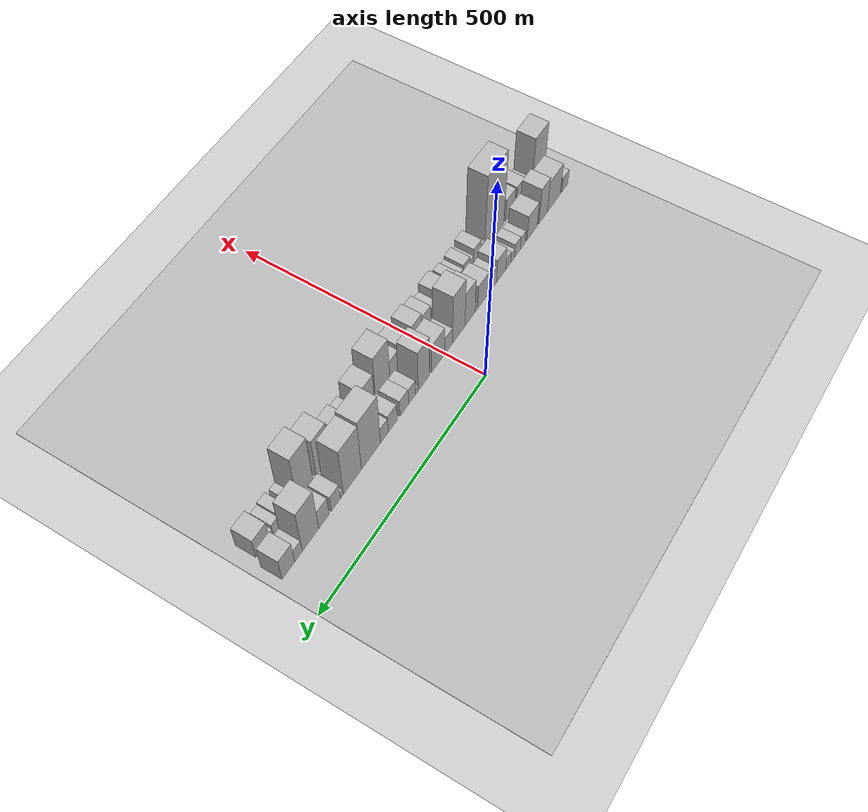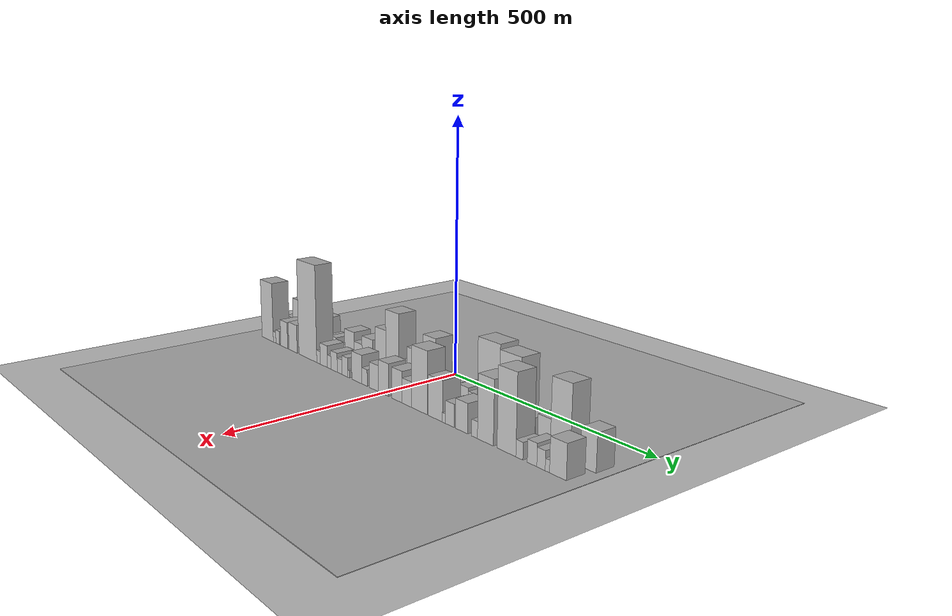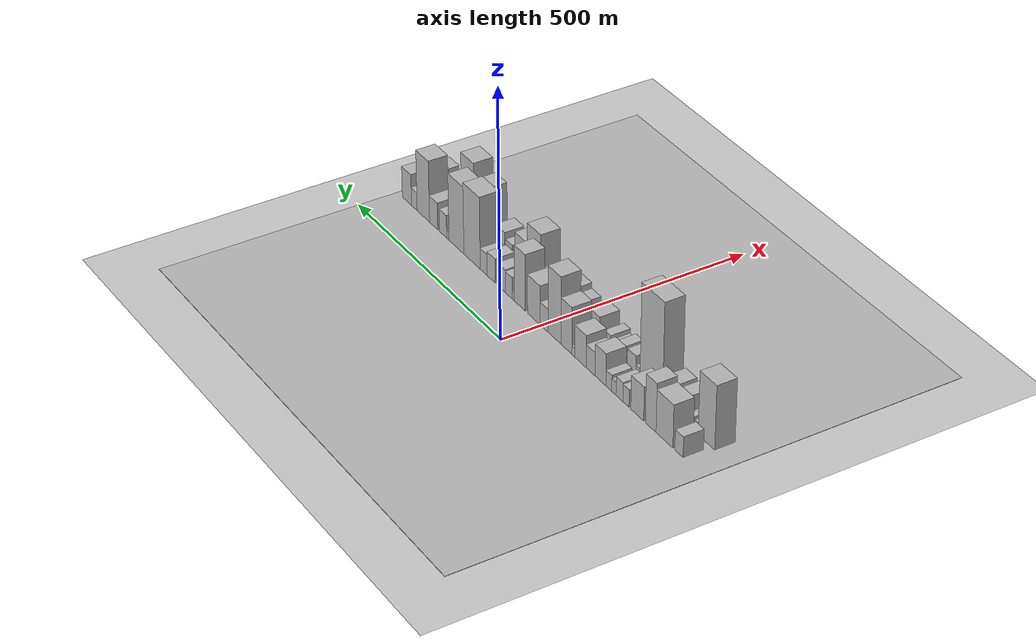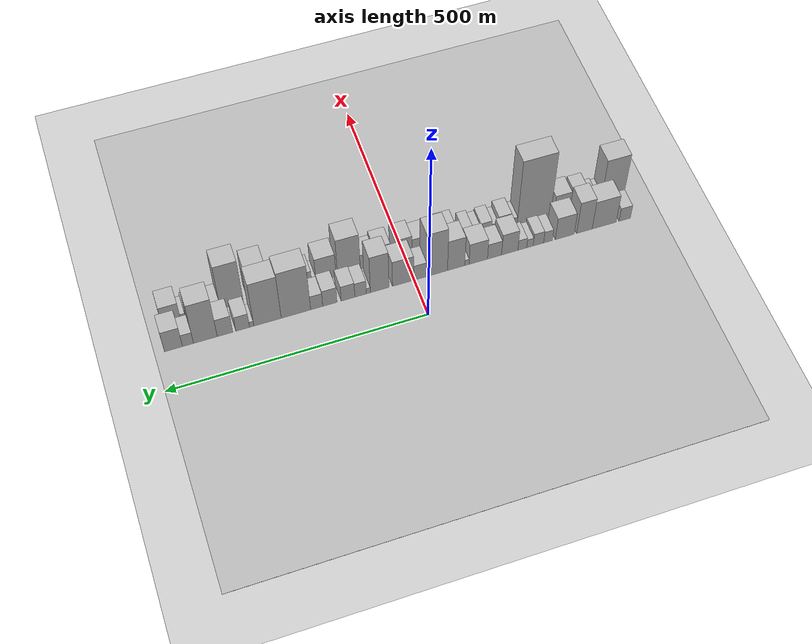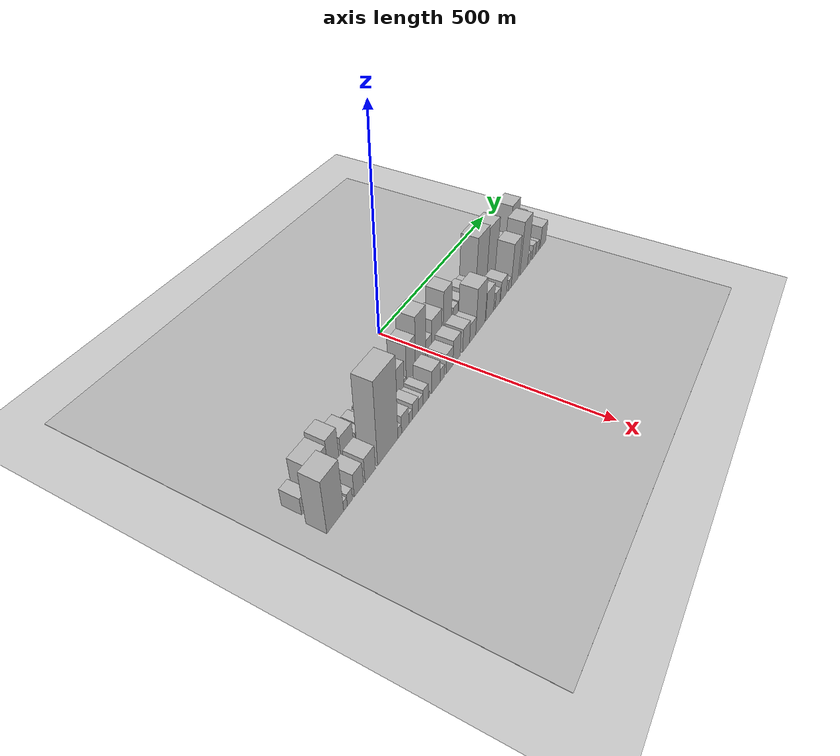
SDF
<?xml version="1.0" encoding="utf-8"?>

<sdf version="1.6">

   <world name="default">

      <gui fullscreen="0">

         <camera name="user_camera">

            <pose>-15 0 4.57585 0 0 0</pose>

            <view_controller>orbit</view_controller>

         </camera>

      </gui>

      <scene>

         <sky>

           <clouds>

             <speed>12</speed>

           </clouds>

         </sky>

         <ambient>0.4 0.4 0.4 1</ambient>

         <background>0.7 0.7 0.7 1</background>

         <shadows>1</shadows>

      </scene>

      <gravity>0 0 -9.8066</gravity>

      <magnetic_field>6e-06 2.3e-05 -4.2e-05</magnetic_field>

      <physics default="0" name="default_physics" type="ode">

         <ode>

            <solver>

               <type>quick</type>

               <iters>10</iters>

               <sor>1.0</sor>

               <use_dynamic_moi_rescaling>0</use_dynamic_moi_rescaling>

            </solver>

            <constraints>

               <cfm>0</cfm>

               <erp>0.2</erp>

               <contact_max_correcting_vel>100</contact_max_correcting_vel>

               <contact_surface_layer>0.001</contact_surface_layer>

            </constraints>

         </ode>

         <max_step_size>0.004</max_step_size>

         <real_time_factor>1</real_time_factor>

         <real_time_update_rate>250</real_time_update_rate>

      </physics>

      <light name="sun" type="directional">

         <cast_shadows>1</cast_shadows>

         <pose>0 0 10 0 0 0</pose>

         <diffuse>0.8 0.8 0.8 1</diffuse>

         <specular>0.2 0.2 0.2 1</specular>

         <attenuation>

            <range>1000</range>

            <constant>0.9</constant>

            <linear>0.01</linear>

            <quadratic>0.001</quadratic>

         </attenuation>

         <direction>-0.5 0.1 -0.9</direction>

      </light>

      <include>

         <name>ground_plane_1</name>

         <uri>model://HANNAS_ground_plane</uri>

         <pose>0 0 0  0 0 0</pose>

      </include>

      <include>

         <name>ground_plane_2</name>

         <uri>model://HANNAS_ground_plane</uri>

         <pose>100 0 0  0 0 0</pose>

      </include>

      <model name="building_1">

         <static>1</static>

         <pose frame="">100.0000 -428.0679 0 0.000000 0.000000 0.000000</pose>

         <link name="link">

            <pose frame="">0 0 21.00 0 0 0</pose>

            <collision name="collision">

               <geometry>

                  <box>

                     <size>40.0000 23.8642 42.0000</size>

                  </box>

               </geometry>

               <max_contacts>10</max_contacts>

               <surface>

                  <contact>

                     <ode/>

                  </contact>

                  <bounce/>

                  <friction>

                     <torsional>

                        <ode/>

                     </torsional>

                     <ode/>

                  </friction>

               </surface>

            </collision>

            <visual name="visual">

               <cast_shadows>0</cast_shadows>

               <geometry>

                  <box>

                     <size>40.0000 23.8642 42.0000</size>

                  </box>

               </geometry>

               <material>

                  <script>

                     <uri>model://HANNAS_wall/materials/scripts</uri>

                     <uri>model://HANNAS_wall/materials/textures</uri>

                     <name>vrc/HANNAS_wall</name>

                  </script>

               </material>

            </visual>

            <self_collide>0</self_collide>

            <enable_wind>0</enable_wind>

            <kinematic>0</kinematic>

         </link>

      </model>

      <model name="building_2">

         <static>1</static>

         <pose frame="">100.0000 -385.1828 0 0.000000 0.000000 0.000000</pose>

         <link name="link">

            <pose frame="">0 0 43.50 0 0 0</pose>

            <collision name="collision">

               <geometry>

                  <box>

                     <size>40.0000 49.9060 87.0000</size>

                  </box>

               </geometry>

               <max_contacts>10</max_contacts>

               <surface>

                  <contact>

                     <ode/>

                  </contact>

                  <bounce/>

                  <friction>

                     <torsional>

                        <ode/>

                     </torsional>

                     <ode/>

                  </friction>

               </surface>

            </collision>

            <visual name="visual">

               <cast_shadows>0</cast_shadows>

               <geometry>

                  <box>

                     <size>40.0000 49.9060 87.0000</size>

                  </box>

               </geometry>

               <material>

                  <script>

                     <uri>model://HANNAS_wall/materials/scripts</uri>

                     <uri>model://HANNAS_wall/materials/textures</uri>

                     <name>vrc/HANNAS_wall</name>

                  </script>

               </material>

            </visual>

            <self_collide>0</self_collide>

            <enable_wind>0</enable_wind>

            <kinematic>0</kinematic>

         </link>

      </model>

      <model name="building_3">

         <static>1</static>

         <pose frame="">100.0000 -344.1812 0 0.000000 0.000000 0.000000</pose>

         <link name="link">

            <pose frame="">0 0 49.50 0 0 0</pose>

            <collision name="collision">

               <geometry>

                  <box>

                     <size>40.0000 32.0972 99.0000</size>

                  </box>

               </geometry>

               <max_contacts>10</max_contacts>

               <surface>

                  <contact>

                     <ode/>

                  </contact>

                  <bounce/>

                  <friction>

                     <torsional>

                        <ode/>

                     </torsional>

                     <ode/>

                  </friction>

               </surface>

            </collision>

            <visual name="visual">

               <cast_shadows>0</cast_shadows>

               <geometry>

                  <box>

                     <size>40.0000 32.0972 99.0000</size>

                  </box>

               </geometry>

               <material>

                  <script>

                     <uri>model://HANNAS_wall/materials/scripts</uri>

                     <uri>model://HANNAS_wall/materials/textures</uri>

                     <name>vrc/HANNAS_wall</name>

                  </script>

               </material>

            </visual>

            <self_collide>0</self_collide>

            <enable_wind>0</enable_wind>

            <kinematic>0</kinematic>

         </link>

      </model>

      <model name="building_4">

         <static>1</static>

         <pose frame="">100.0000 -303.6838 0 0.000000 0.000000 0.000000</pose>

         <link name="link">

            <pose frame="">0 0 34.50 0 0 0</pose>

            <collision name="collision">

               <geometry>

                  <box>

                     <size>40.0000 38.8975 69.0000</size>

                  </box>

               </geometry>

               <max_contacts>10</max_contacts>

               <surface>

                  <contact>

                     <ode/>

                  </contact>

                  <bounce/>

                  <friction>

                     <torsional>

                        <ode/>

                     </torsional>

                     <ode/>

                  </friction>

               </surface>

            </collision>

            <visual name="visual">

               <cast_shadows>0</cast_shadows>

               <geometry>

                  <box>

                     <size>40.0000 38.8975 69.0000</size>

                  </box>

               </geometry>

               <material>

                  <script>

                     <uri>model://HANNAS_wall/materials/scripts</uri>

                     <uri>model://HANNAS_wall/materials/textures</uri>

                     <name>vrc/HANNAS_wall</name>

                  </script>

               </material>

            </visual>

            <self_collide>0</self_collide>

            <enable_wind>0</enable_wind>

            <kinematic>0</kinematic>

         </link>

      </model>

      <model name="building_5">

         <static>1</static>

         <pose frame="">100.0000 -269.1361 0 0.000000 0.000000 0.000000</pose>

         <link name="link">

            <pose frame="">0 0 18.00 0 0 0</pose>

            <collision name="collision">

               <geometry>

                  <box>

                     <size>40.0000 18.1979 36.0000</size>

                  </box>

               </geometry>

               <max_contacts>10</max_contacts>

               <surface>

                  <contact>

                     <ode/>

                  </contact>

                  <bounce/>

                  <friction>

                     <torsional>

                        <ode/>

                     </torsional>

                     <ode/>

                  </friction>

               </surface>

            </collision>

            <visual name="visual">

               <cast_shadows>0</cast_shadows>

               <geometry>

                  <box>

                     <size>40.0000 18.1979 36.0000</size>

                  </box>

               </geometry>

               <material>

                  <script>

                     <uri>model://HANNAS_wall/materials/scripts</uri>

                     <uri>model://HANNAS_wall/materials/textures</uri>

                     <name>vrc/HANNAS_wall</name>

                  </script>

               </material>

            </visual>

            <self_collide>0</self_collide>

            <enable_wind>0</enable_wind>

            <kinematic>0</kinematic>

         </link>

      </model>

      <model name="building_6">

         <static>1</static>

         <pose frame="">100.0000 -249.3379 0 0.000000 0.000000 0.000000</pose>

         <link name="link">

            <pose frame="">0 0 19.50 0 0 0</pose>

            <collision name="collision">

               <geometry>

                  <box>

                     <size>40.0000 21.3986 39.0000</size>

                  </box>

               </geometry>

               <max_contacts>10</max_contacts>

               <surface>

                  <contact>

                     <ode/>

                  </contact>

                  <bounce/>

                  <friction>

                     <torsional>

                        <ode/>

                     </torsional>

                     <ode/>

                  </friction>

               </surface>

            </collision>

            <visual name="visual">

               <cast_shadows>0</cast_shadows>

               <geometry>

                  <box>

                     <size>40.0000 21.3986 39.0000</size>

                  </box>

               </geometry>

               <material>

                  <script>

                     <uri>model://HANNAS_wall/materials/scripts</uri>

                     <uri>model://HANNAS_wall/materials/textures</uri>

                     <name>vrc/HANNAS_wall</name>

                  </script>

               </material>

            </visual>

            <self_collide>0</self_collide>

            <enable_wind>0</enable_wind>

            <kinematic>0</kinematic>

         </link>

      </model>

      <model name="building_7">

         <static>1</static>

         <pose frame="">100.0000 -232.1086 0 0.000000 0.000000 0.000000</pose>

         <link name="link">

            <pose frame="">0 0 13.50 0 0 0</pose>

            <collision name="collision">

               <geometry>

                  <box>

                     <size>40.0000 13.0601 27.0000</size>

                  </box>

               </geometry>

               <max_contacts>10</max_contacts>

               <surface>

                  <contact>

                     <ode/>

                  </contact>

                  <bounce/>

                  <friction>

                     <torsional>

                        <ode/>

                     </torsional>

                     <ode/>

                  </friction>

               </surface>

            </collision>

            <visual name="visual">

               <cast_shadows>0</cast_shadows>

               <geometry>

                  <box>

                     <size>40.0000 13.0601 27.0000</size>

                  </box>

               </geometry>

               <material>

                  <script>

                     <uri>model://HANNAS_wall/materials/scripts</uri>

                     <uri>model://HANNAS_wall/materials/textures</uri>

                     <name>vrc/HANNAS_wall</name>

                  </script>

               </material>

            </visual>

            <self_collide>0</self_collide>

            <enable_wind>0</enable_wind>

            <kinematic>0</kinematic>

         </link>

      </model>

      <model name="building_8">

         <static>1</static>

         <pose frame="">100.0000 -216.5394 0 0.000000 0.000000 0.000000</pose>

         <link name="link">

            <pose frame="">0 0 16.50 0 0 0</pose>

            <collision name="collision">

               <geometry>

                  <box>

                     <size>40.0000 18.0782 33.0000</size>

                  </box>

               </geometry>

               <max_contacts>10</max_contacts>

               <surface>

                  <contact>

                     <ode/>

                  </contact>

                  <bounce/>

                  <friction>

                     <torsional>

                        <ode/>

                     </torsional>

                     <ode/>

                  </friction>

               </surface>

            </collision>

            <visual name="visual">

               <cast_shadows>0</cast_shadows>

               <geometry>

                  <box>

                     <size>40.0000 18.0782 33.0000</size>

                  </box>

               </geometry>

               <material>

                  <script>

                     <uri>model://HANNAS_wall/materials/scripts</uri>

                     <uri>model://HANNAS_wall/materials/textures</uri>

                     <name>vrc/HANNAS_wall</name>

                  </script>

               </material>

            </visual>

            <self_collide>0</self_collide>

            <enable_wind>0</enable_wind>

            <kinematic>0</kinematic>

         </link>

      </model>

      <model name="building_9">

         <static>1</static>

         <pose frame="">100.0000 -190.8295 0 0.000000 0.000000 0.000000</pose>

         <link name="link">

            <pose frame="">0 0 33.00 0 0 0</pose>

            <collision name="collision">

               <geometry>

                  <box>

                     <size>40.0000 33.3417 66.0000</size>

                  </box>

               </geometry>

               <max_contacts>10</max_contacts>

               <surface>

                  <contact>

                     <ode/>

                  </contact>

                  <bounce/>

                  <friction>

                     <torsional>

                        <ode/>

                     </torsional>

                     <ode/>

                  </friction>

               </surface>

            </collision>

            <visual name="visual">

               <cast_shadows>0</cast_shadows>

               <geometry>

                  <box>

                     <size>40.0000 33.3417 66.0000</size>

                  </box>

               </geometry>

               <material>

                  <script>

                     <uri>model://HANNAS_wall/materials/scripts</uri>

                     <uri>model://HANNAS_wall/materials/textures</uri>

                     <name>vrc/HANNAS_wall</name>

                  </script>

               </material>

            </visual>

            <self_collide>0</self_collide>

            <enable_wind>0</enable_wind>

            <kinematic>0</kinematic>

         </link>

      </model>

      <model name="building_10">

         <static>1</static>

         <pose frame="">100.0000 -159.9764 0 0.000000 0.000000 0.000000</pose>

         <link name="link">

            <pose frame="">0 0 24.00 0 0 0</pose>

            <collision name="collision">

               <geometry>

                  <box>

                     <size>40.0000 28.3645 48.0000</size>

                  </box>

               </geometry>

               <max_contacts>10</max_contacts>

               <surface>

                  <contact>

                     <ode/>

                  </contact>

                  <bounce/>

                  <friction>

                     <torsional>

                        <ode/>

                     </torsional>

                     <ode/>

                  </friction>

               </surface>

            </collision>

            <visual name="visual">

               <cast_shadows>0</cast_shadows>

               <geometry>

                  <box>

                     <size>40.0000 28.3645 48.0000</size>

                  </box>

               </geometry>

               <material>

                  <script>

                     <uri>model://HANNAS_wall/materials/scripts</uri>

                     <uri>model://HANNAS_wall/materials/textures</uri>

                     <name>vrc/HANNAS_wall</name>

                  </script>

               </material>

            </visual>

            <self_collide>0</self_collide>

            <enable_wind>0</enable_wind>

            <kinematic>0</kinematic>

         </link>

      </model>

      <model name="building_11">

         <static>1</static>

         <pose frame="">100.0000 -127.2238 0 0.000000 0.000000 0.000000</pose>

         <link name="link">

            <pose frame="">0 0 33.00 0 0 0</pose>

            <collision name="collision">

               <geometry>

                  <box>

                     <size>40.0000 37.1406 66.0000</size>

                  </box>

               </geometry>

               <max_contacts>10</max_contacts>

               <surface>

                  <contact>

                     <ode/>

                  </contact>

                  <bounce/>

                  <friction>

                     <torsional>

                        <ode/>

                     </torsional>

                     <ode/>

                  </friction>

               </surface>

            </collision>

            <visual name="visual">

               <cast_shadows>0</cast_shadows>

               <geometry>

                  <box>

                     <size>40.0000 37.1406 66.0000</size>

                  </box>

               </geometry>

               <material>

                  <script>

                     <uri>model://HANNAS_wall/materials/scripts</uri>

                     <uri>model://HANNAS_wall/materials/textures</uri>

                     <name>vrc/HANNAS_wall</name>

                  </script>

               </material>

            </visual>

            <self_collide>0</self_collide>

            <enable_wind>0</enable_wind>

            <kinematic>0</kinematic>

         </link>

      </model>

      <model name="building_12">

         <static>1</static>

         <pose frame="">100.0000 -104.2451 0 0.000000 0.000000 0.000000</pose>

         <link name="link">

            <pose frame="">0 0 9.00 0 0 0</pose>

            <collision name="collision">

               <geometry>

                  <box>

                     <size>40.0000 8.8168 18.0000</size>

                  </box>

               </geometry>

               <max_contacts>10</max_contacts>

               <surface>

                  <contact>

                     <ode/>

                  </contact>

                  <bounce/>

                  <friction>

                     <torsional>

                        <ode/>

                     </torsional>

                     <ode/>

                  </friction>

               </surface>

            </collision>

            <visual name="visual">

               <cast_shadows>0</cast_shadows>

               <geometry>

                  <box>

                     <size>40.0000 8.8168 18.0000</size>

                  </box>

               </geometry>

               <material>

                  <script>

                     <uri>model://HANNAS_wall/materials/scripts</uri>

                     <uri>model://HANNAS_wall/materials/textures</uri>

                     <name>vrc/HANNAS_wall</name>

                  </script>

               </material>

            </visual>

            <self_collide>0</self_collide>

            <enable_wind>0</enable_wind>

            <kinematic>0</kinematic>

         </link>

      </model>

      <model name="building_13">

         <static>1</static>

         <pose frame="">100.0000 -82.5706 0 0.000000 0.000000 0.000000</pose>

         <link name="link">

            <pose frame="">0 0 48.00 0 0 0</pose>

            <collision name="collision">

               <geometry>

                  <box>

                     <size>40.0000 34.5321 96.0000</size>

                  </box>

               </geometry>

               <max_contacts>10</max_contacts>

               <surface>

                  <contact>

                     <ode/>

                  </contact>

                  <bounce/>

                  <friction>

                     <torsional>

                        <ode/>

                     </torsional>

                     <ode/>

                  </friction>

               </surface>

            </collision>

            <visual name="visual">

               <cast_shadows>0</cast_shadows>

               <geometry>

                  <box>

                     <size>40.0000 34.5321 96.0000</size>

                  </box>

               </geometry>

               <material>

                  <script>

                     <uri>model://HANNAS_wall/materials/scripts</uri>

                     <uri>model://HANNAS_wall/materials/textures</uri>

                     <name>vrc/HANNAS_wall</name>

                  </script>

               </material>

            </visual>

            <self_collide>0</self_collide>

            <enable_wind>0</enable_wind>

            <kinematic>0</kinematic>

         </link>

      </model>

      <model name="building_14">

         <static>1</static>

         <pose frame="">100.0000 -44.4450 0 0.000000 0.000000 0.000000</pose>

         <link name="link">

            <pose frame="">0 0 69.00 0 0 0</pose>

            <collision name="collision">

               <geometry>

                  <box>

                     <size>40.0000 41.7192 138.0000</size>

                  </box>

               </geometry>

               <max_contacts>10</max_contacts>

               <surface>

                  <contact>

                     <ode/>

                  </contact>

                  <bounce/>

                  <friction>

                     <torsional>

                        <ode/>

                     </torsional>

                     <ode/>

                  </friction>

               </surface>

            </collision>

            <visual name="visual">

               <cast_shadows>0</cast_shadows>

               <geometry>

                  <box>

                     <size>40.0000 41.7192 138.0000</size>

                  </box>

               </geometry>

               <material>

                  <script>

                     <uri>model://HANNAS_wall/materials/scripts</uri>

                     <uri>model://HANNAS_wall/materials/textures</uri>

                     <name>vrc/HANNAS_wall</name>

                  </script>

               </material>

            </visual>

            <self_collide>0</self_collide>

            <enable_wind>0</enable_wind>

            <kinematic>0</kinematic>

         </link>

      </model>

      <model name="building_15">

         <static>1</static>

         <pose frame="">100.0000 -10.7258 0 0.000000 0.000000 0.000000</pose>

         <link name="link">

            <pose frame="">0 0 24.00 0 0 0</pose>

            <collision name="collision">

               <geometry>

                  <box>

                     <size>40.0000 25.7191 48.0000</size>

                  </box>

               </geometry>

               <max_contacts>10</max_contacts>

               <surface>

                  <contact>

                     <ode/>

                  </contact>

                  <bounce/>

                  <friction>

                     <torsional>

                        <ode/>

                     </torsional>

                     <ode/>

                  </friction>

               </surface>

            </collision>

            <visual name="visual">

               <cast_shadows>0</cast_shadows>

               <geometry>

                  <box>

                     <size>40.0000 25.7191 48.0000</size>

                  </box>

               </geometry>

               <material>

                  <script>

                     <uri>model://HANNAS_wall/materials/scripts</uri>

                     <uri>model://HANNAS_wall/materials/textures</uri>

                     <name>vrc/HANNAS_wall</name>

                  </script>

               </material>

            </visual>

            <self_collide>0</self_collide>

            <enable_wind>0</enable_wind>

            <kinematic>0</kinematic>

         </link>

      </model>

      <model name="building_16">

         <static>1</static>

         <pose frame="">100.0000 23.0376 0 0.000000 0.000000 0.000000</pose>

         <link name="link">

            <pose frame="">0 0 40.50 0 0 0</pose>

            <collision name="collision">

               <geometry>

                  <box>

                     <size>40.0000 41.8078 81.0000</size>

                  </box>

               </geometry>

               <max_contacts>10</max_contacts>

               <surface>

                  <contact>

                     <ode/>

                  </contact>

                  <bounce/>

                  <friction>

                     <torsional>

                        <ode/>

                     </torsional>

                     <ode/>

                  </friction>

               </surface>

            </collision>

            <visual name="visual">

               <cast_shadows>0</cast_shadows>

               <geometry>

                  <box>

                     <size>40.0000 41.8078 81.0000</size>

                  </box>

               </geometry>

               <material>

                  <script>

                     <uri>model://HANNAS_wall/materials/scripts</uri>

                     <uri>model://HANNAS_wall/materials/textures</uri>

                     <name>vrc/HANNAS_wall</name>

                  </script>

               </material>

            </visual>

            <self_collide>0</self_collide>

            <enable_wind>0</enable_wind>

            <kinematic>0</kinematic>

         </link>

      </model>

      <model name="building_17">

         <static>1</static>

         <pose frame="">100.0000 69.2040 0 0.000000 0.000000 0.000000</pose>

         <link name="link">

            <pose frame="">0 0 58.50 0 0 0</pose>

            <collision name="collision">

               <geometry>

                  <box>

                     <size>40.0000 36.5250 117.0000</size>

                  </box>

               </geometry>

               <max_contacts>10</max_contacts>

               <surface>

                  <contact>

                     <ode/>

                  </contact>

                  <bounce/>

                  <friction>

                     <torsional>

                        <ode/>

                     </torsional>

                     <ode/>

                  </friction>

               </surface>

            </collision>

            <visual name="visual">

               <cast_shadows>0</cast_shadows>

               <geometry>

                  <box>

                     <size>40.0000 36.5250 117.0000</size>

                  </box>

               </geometry>

               <material>

                  <script>

                     <uri>model://HANNAS_wall/materials/scripts</uri>

                     <uri>model://HANNAS_wall/materials/textures</uri>

                     <name>vrc/HANNAS_wall</name>

                  </script>

               </material>

            </visual>

            <self_collide>0</self_collide>

            <enable_wind>0</enable_wind>

            <kinematic>0</kinematic>

         </link>

      </model>

      <model name="building_18">

         <static>1</static>

         <pose frame="">100.0000 91.3263 0 0.000000 0.000000 0.000000</pose>

         <link name="link">

            <pose frame="">0 0 9.00 0 0 0</pose>

            <collision name="collision">

               <geometry>

                  <box>

                     <size>40.0000 7.7197 18.0000</size>

                  </box>

               </geometry>

               <max_contacts>10</max_contacts>

               <surface>

                  <contact>

                     <ode/>

                  </contact>

                  <bounce/>

                  <friction>

                     <torsional>

                        <ode/>

                     </torsional>

                     <ode/>

                  </friction>

               </surface>

            </collision>

            <visual name="visual">

               <cast_shadows>0</cast_shadows>

               <geometry>

                  <box>

                     <size>40.0000 7.7197 18.0000</size>

                  </box>

               </geometry>

               <material>

                  <script>

                     <uri>model://HANNAS_wall/materials/scripts</uri>

                     <uri>model://HANNAS_wall/materials/textures</uri>

                     <name>vrc/HANNAS_wall</name>

                  </script>

               </material>

            </visual>

            <self_collide>0</self_collide>

            <enable_wind>0</enable_wind>

            <kinematic>0</kinematic>

         </link>

      </model>

      <model name="building_19">

         <static>1</static>

         <pose frame="">100.0000 106.5233 0 0.000000 0.000000 0.000000</pose>

         <link name="link">

            <pose frame="">0 0 22.50 0 0 0</pose>

            <collision name="collision">

               <geometry>

                  <box>

                     <size>40.0000 22.6743 45.0000</size>

                  </box>

               </geometry>

               <max_contacts>10</max_contacts>

               <surface>

                  <contact>

                     <ode/>

                  </contact>

                  <bounce/>

                  <friction>

                     <torsional>

                        <ode/>

                     </torsional>

                     <ode/>

                  </friction>

               </surface>

            </collision>

            <visual name="visual">

               <cast_shadows>0</cast_shadows>

               <geometry>

                  <box>

                     <size>40.0000 22.6743 45.0000</size>

                  </box>

               </geometry>

               <material>

                  <script>

                     <uri>model://HANNAS_wall/materials/scripts</uri>

                     <uri>model://HANNAS_wall/materials/textures</uri>

                     <name>vrc/HANNAS_wall</name>

                  </script>

               </material>

            </visual>

            <self_collide>0</self_collide>

            <enable_wind>0</enable_wind>

            <kinematic>0</kinematic>

         </link>

      </model>

      <model name="building_20">

         <static>1</static>

         <pose frame="">100.0000 131.1796 0 0.000000 0.000000 0.000000</pose>

         <link name="link">

            <pose frame="">0 0 24.00 0 0 0</pose>

            <collision name="collision">

               <geometry>

                  <box>

                     <size>40.0000 26.6383 48.0000</size>

                  </box>

               </geometry>

               <max_contacts>10</max_contacts>

               <surface>

                  <contact>

                     <ode/>

                  </contact>

                  <bounce/>

                  <friction>

                     <torsional>

                        <ode/>

                     </torsional>

                     <ode/>

                  </friction>

               </surface>

            </collision>

            <visual name="visual">

               <cast_shadows>0</cast_shadows>

               <geometry>

                  <box>

                     <size>40.0000 26.6383 48.0000</size>

                  </box>

               </geometry>

               <material>

                  <script>

                     <uri>model://HANNAS_wall/materials/scripts</uri>

                     <uri>model://HANNAS_wall/materials/textures</uri>

                     <name>vrc/HANNAS_wall</name>

                  </script>

               </material>

            </visual>

            <self_collide>0</self_collide>

            <enable_wind>0</enable_wind>

            <kinematic>0</kinematic>

         </link>

      </model>

      <model name="building_21">

         <static>1</static>

         <pose frame="">100.0000 166.3800 0 0.000000 0.000000 0.000000</pose>

         <link name="link">

            <pose frame="">0 0 25.50 0 0 0</pose>

            <collision name="collision">

               <geometry>

                  <box>

                     <size>40.0000 27.7625 51.0000</size>

                  </box>

               </geometry>

               <max_contacts>10</max_contacts>

               <surface>

                  <contact>

                     <ode/>

                  </contact>

                  <bounce/>

                  <friction>

                     <torsional>

                        <ode/>

                     </torsional>

                     <ode/>

                  </friction>

               </surface>

            </collision>

            <visual name="visual">

               <cast_shadows>0</cast_shadows>

               <geometry>

                  <box>

                     <size>40.0000 27.7625 51.0000</size>

                  </box>

               </geometry>

               <material>

                  <script>

                     <uri>model://HANNAS_wall/materials/scripts</uri>

                     <uri>model://HANNAS_wall/materials/textures</uri>

                     <name>vrc/HANNAS_wall</name>

                  </script>

               </material>

            </visual>

            <self_collide>0</self_collide>

            <enable_wind>0</enable_wind>

            <kinematic>0</kinematic>

         </link>

      </model>

      <model name="building_22">

         <static>1</static>

         <pose frame="">100.0000 191.9842 0 0.000000 0.000000 0.000000</pose>

         <link name="link">

            <pose frame="">0 0 22.50 0 0 0</pose>

            <collision name="collision">

               <geometry>

                  <box>

                     <size>40.0000 23.4460 45.0000</size>

                  </box>

               </geometry>

               <max_contacts>10</max_contacts>

               <surface>

                  <contact>

                     <ode/>

                  </contact>

                  <bounce/>

                  <friction>

                     <torsional>

                        <ode/>

                     </torsional>

                     <ode/>

                  </friction>

               </surface>

            </collision>

            <visual name="visual">

               <cast_shadows>0</cast_shadows>

               <geometry>

                  <box>

                     <size>40.0000 23.4460 45.0000</size>

                  </box>

               </geometry>

               <material>

                  <script>

                     <uri>model://HANNAS_wall/materials/scripts</uri>

                     <uri>model://HANNAS_wall/materials/textures</uri>

                     <name>vrc/HANNAS_wall</name>

                  </script>

               </material>

            </visual>

            <self_collide>0</self_collide>

            <enable_wind>0</enable_wind>

            <kinematic>0</kinematic>

         </link>

      </model>

      <model name="building_23">

         <static>1</static>

         <pose frame="">100.0000 231.9774 0 0.000000 0.000000 0.000000</pose>

         <link name="link">

            <pose frame="">0 0 75.00 0 0 0</pose>

            <collision name="collision">

               <geometry>

                  <box>

                     <size>40.0000 56.5404 150.0000</size>

                  </box>

               </geometry>

               <max_contacts>10</max_contacts>

               <surface>

                  <contact>

                     <ode/>

                  </contact>

                  <bounce/>

                  <friction>

                     <torsional>

                        <ode/>

                     </torsional>

                     <ode/>

                  </friction>

               </surface>

            </collision>

            <visual name="visual">

               <cast_shadows>0</cast_shadows>

               <geometry>

                  <box>

                     <size>40.0000 56.5404 150.0000</size>

                  </box>

               </geometry>

               <material>

                  <script>

                     <uri>model://HANNAS_wall/materials/scripts</uri>

                     <uri>model://HANNAS_wall/materials/textures</uri>

                     <name>vrc/HANNAS_wall</name>

                  </script>

               </material>

            </visual>

            <self_collide>0</self_collide>

            <enable_wind>0</enable_wind>

            <kinematic>0</kinematic>

         </link>

      </model>

      <model name="building_24">

         <static>1</static>

         <pose frame="">100.0000 286.4986 0 0.000000 0.000000 0.000000</pose>

         <link name="link">

            <pose frame="">0 0 70.50 0 0 0</pose>

            <collision name="collision">

               <geometry>

                  <box>

                     <size>40.0000 52.5019 141.0000</size>

                  </box>

               </geometry>

               <max_contacts>10</max_contacts>

               <surface>

                  <contact>

                     <ode/>

                  </contact>

                  <bounce/>

                  <friction>

                     <torsional>

                        <ode/>

                     </torsional>

                     <ode/>

                  </friction>

               </surface>

            </collision>

            <visual name="visual">

               <cast_shadows>0</cast_shadows>

               <geometry>

                  <box>

                     <size>40.0000 52.5019 141.0000</size>

                  </box>

               </geometry>

               <material>

                  <script>

                     <uri>model://HANNAS_wall/materials/scripts</uri>

                     <uri>model://HANNAS_wall/materials/textures</uri>

                     <name>vrc/HANNAS_wall</name>

                  </script>

               </material>

            </visual>

            <self_collide>0</self_collide>

            <enable_wind>0</enable_wind>

            <kinematic>0</kinematic>

         </link>

      </model>

      <model name="building_25">

         <static>1</static>

         <pose frame="">100.0000 316.8146 0 0.000000 0.000000 0.000000</pose>

         <link name="link">

            <pose frame="">0 0 9.00 0 0 0</pose>

            <collision name="collision">

               <geometry>

                  <box>

                     <size>40.0000 8.1301 18.0000</size>

                  </box>

               </geometry>

               <max_contacts>10</max_contacts>

               <surface>

                  <contact>

                     <ode/>

                  </contact>

                  <bounce/>

                  <friction>

                     <torsional>

                        <ode/>

                     </torsional>

                     <ode/>

                  </friction>

               </surface>

            </collision>

            <visual name="visual">

               <cast_shadows>0</cast_shadows>

               <geometry>

                  <box>

                     <size>40.0000 8.1301 18.0000</size>

                  </box>

               </geometry>

               <material>

                  <script>

                     <uri>model://HANNAS_wall/materials/scripts</uri>

                     <uri>model://HANNAS_wall/materials/textures</uri>

                     <name>vrc/HANNAS_wall</name>

                  </script>

               </material>

            </visual>

            <self_collide>0</self_collide>

            <enable_wind>0</enable_wind>

            <kinematic>0</kinematic>

         </link>

      </model>

      <model name="building_26">

         <static>1</static>

         <pose frame="">100.0000 333.9260 0 0.000000 0.000000 0.000000</pose>

         <link name="link">

            <pose frame="">0 0 24.00 0 0 0</pose>

            <collision name="collision">

               <geometry>

                  <box>

                     <size>40.0000 26.0927 48.0000</size>

                  </box>

               </geometry>

               <max_contacts>10</max_contacts>

               <surface>

                  <contact>

                     <ode/>

                  </contact>

                  <bounce/>

                  <friction>

                     <torsional>

                        <ode/>

                     </torsional>

                     <ode/>

                  </friction>

               </surface>

            </collision>

            <visual name="visual">

               <cast_shadows>0</cast_shadows>

               <geometry>

                  <box>

                     <size>40.0000 26.0927 48.0000</size>

                  </box>

               </geometry>

               <material>

                  <script>

                     <uri>model://HANNAS_wall/materials/scripts</uri>

                     <uri>model://HANNAS_wall/materials/textures</uri>

                     <name>vrc/HANNAS_wall</name>

                  </script>

               </material>

            </visual>

            <self_collide>0</self_collide>

            <enable_wind>0</enable_wind>

            <kinematic>0</kinematic>

         </link>

      </model>

      <model name="building_27">

         <static>1</static>

         <pose frame="">100.0000 367.5840 0 0.000000 0.000000 0.000000</pose>

         <link name="link">

            <pose frame="">0 0 28.50 0 0 0</pose>

            <collision name="collision">

               <geometry>

                  <box>

                     <size>40.0000 29.2233 57.0000</size>

                  </box>

               </geometry>

               <max_contacts>10</max_contacts>

               <surface>

                  <contact>

                     <ode/>

                  </contact>

                  <bounce/>

                  <friction>

                     <torsional>

                        <ode/>

                     </torsional>

                     <ode/>

                  </friction>

               </surface>

            </collision>

            <visual name="visual">

               <cast_shadows>0</cast_shadows>

               <geometry>

                  <box>

                     <size>40.0000 29.2233 57.0000</size>

                  </box>

               </geometry>

               <material>

                  <script>

                     <uri>model://HANNAS_wall/materials/scripts</uri>

                     <uri>model://HANNAS_wall/materials/textures</uri>

                     <name>vrc/HANNAS_wall</name>

                  </script>

               </material>

            </visual>

            <self_collide>0</self_collide>

            <enable_wind>0</enable_wind>

            <kinematic>0</kinematic>

         </link>

      </model>

      <model name="building_28">

         <static>1</static>

         <pose frame="">100.0000 404.5160 0 0.000000 0.000000 0.000000</pose>

         <link name="link">

            <pose frame="">0 0 64.50 0 0 0</pose>

            <collision name="collision">

               <geometry>

                  <box>

                     <size>40.0000 44.6407 129.0000</size>

                  </box>

               </geometry>

               <max_contacts>10</max_contacts>

               <surface>

                  <contact>

                     <ode/>

                  </contact>

                  <bounce/>

                  <friction>

                     <torsional>

                        <ode/>

                     </torsional>

                     <ode/>

                  </friction>

               </surface>

            </collision>

            <visual name="visual">

               <cast_shadows>0</cast_shadows>

               <geometry>

                  <box>

                     <size>40.0000 44.6407 129.0000</size>

                  </box>

               </geometry>

               <material>

                  <script>

                     <uri>model://HANNAS_wall/materials/scripts</uri>

                     <uri>model://HANNAS_wall/materials/textures</uri>

                     <name>vrc/HANNAS_wall</name>

                  </script>

               </material>

            </visual>

            <self_collide>0</self_collide>

            <enable_wind>0</enable_wind>

            <kinematic>0</kinematic>

         </link>

      </model>

      <model name="building_29">

         <static>1</static>

         <pose frame="">100.0000 437.1853 0 0.000000 0.000000 0.000000</pose>

         <link name="link">

            <pose frame="">0 0 19.50 0 0 0</pose>

            <collision name="collision">

               <geometry>

                  <box>

                     <size>40.0000 20.6978 39.0000</size>

                  </box>

               </geometry>

               <max_contacts>10</max_contacts>

               <surface>

                  <contact>

                     <ode/>

                  </contact>

                  <bounce/>

                  <friction>

                     <torsional>

                        <ode/>

                     </torsional>

                     <ode/>

                  </friction>

               </surface>

            </collision>

            <visual name="visual">

               <cast_shadows>0</cast_shadows>

               <geometry>

                  <box>

                     <size>40.0000 20.6978 39.0000</size>

                  </box>

               </geometry>

               <material>

                  <script>

                     <uri>model://HANNAS_wall/materials/scripts</uri>

                     <uri>model://HANNAS_wall/materials/textures</uri>

                     <name>vrc/HANNAS_wall</name>

                  </script>

               </material>

            </visual>

            <self_collide>0</self_collide>

            <enable_wind>0</enable_wind>

            <kinematic>0</kinematic>

         </link>

      </model>

      <model name="building_30">

         <static>1</static>

         <pose frame="">100.0000 464.4592 0 0.000000 0.000000 0.000000</pose>

         <link name="link">

            <pose frame="">0 0 33.00 0 0 0</pose>

            <collision name="collision">

               <geometry>

                  <box>

                     <size>40.0000 33.8500 66.0000</size>

                  </box>

               </geometry>

               <max_contacts>10</max_contacts>

               <surface>

                  <contact>

                     <ode/>

                  </contact>

                  <bounce/>

                  <friction>

                     <torsional>

                        <ode/>

                     </torsional>

                     <ode/>

                  </friction>

               </surface>

            </collision>

            <visual name="visual">

               <cast_shadows>0</cast_shadows>

               <geometry>

                  <box>

                     <size>40.0000 33.8500 66.0000</size>

                  </box>

               </geometry>

               <material>

                  <script>

                     <uri>model://HANNAS_wall/materials/scripts</uri>

                     <uri>model://HANNAS_wall/materials/textures</uri>

                     <name>vrc/HANNAS_wall</name>

                  </script>

               </material>

            </visual>

            <self_collide>0</self_collide>

            <enable_wind>0</enable_wind>

            <kinematic>0</kinematic>

         </link>

      </model>

      <model name="building_31">

         <static>1</static>

         <pose frame="">155.0000 -425.7676 0 0.000000 0.000000 0.000000</pose>

         <link name="link">

            <pose frame="">0 0 64.50 0 0 0</pose>

            <collision name="collision">

               <geometry>

                  <box>

                     <size>40.0000 48.4648 129.0000</size>

                  </box>

               </geometry>

               <max_contacts>10</max_contacts>

               <surface>

                  <contact>

                     <ode/>

                  </contact>

                  <bounce/>

                  <friction>

                     <torsional>

                        <ode/>

                     </torsional>

                     <ode/>

                  </friction>

               </surface>

            </collision>

            <visual name="visual">

               <cast_shadows>0</cast_shadows>

               <geometry>

                  <box>

                     <size>40.0000 48.4648 129.0000</size>

                  </box>

               </geometry>

               <material>

                  <script>

                     <uri>model://HANNAS_wall/materials/scripts</uri>

                     <uri>model://HANNAS_wall/materials/textures</uri>

                     <name>vrc/HANNAS_wall</name>

                  </script>

               </material>

            </visual>

            <self_collide>0</self_collide>

            <enable_wind>0</enable_wind>

            <kinematic>0</kinematic>

         </link>

      </model>

      <model name="building_32">

         <static>1</static>

         <pose frame="">155.0000 -396.0954 0 0.000000 0.000000 0.000000</pose>

         <link name="link">

            <pose frame="">0 0 12.00 0 0 0</pose>

            <collision name="collision">

               <geometry>

                  <box>

                     <size>40.0000 10.8796 24.0000</size>

                  </box>

               </geometry>

               <max_contacts>10</max_contacts>

               <surface>

                  <contact>

                     <ode/>

                  </contact>

                  <bounce/>

                  <friction>

                     <torsional>

                        <ode/>

                     </torsional>

                     <ode/>

                  </friction>

               </surface>

            </collision>

            <visual name="visual">

               <cast_shadows>0</cast_shadows>

               <geometry>

                  <box>

                     <size>40.0000 10.8796 24.0000</size>

                  </box>

               </geometry>

               <material>

                  <script>

                     <uri>model://HANNAS_wall/materials/scripts</uri>

                     <uri>model://HANNAS_wall/materials/textures</uri>

                     <name>vrc/HANNAS_wall</name>

                  </script>

               </material>

            </visual>

            <self_collide>0</self_collide>

            <enable_wind>0</enable_wind>

            <kinematic>0</kinematic>

         </link>

      </model>

      <model name="building_33">

         <static>1</static>

         <pose frame="">155.0000 -382.8554 0 0.000000 0.000000 0.000000</pose>

         <link name="link">

            <pose frame="">0 0 15.00 0 0 0</pose>

            <collision name="collision">

               <geometry>

                  <box>

                     <size>40.0000 15.6004 30.0000</size>

                  </box>

               </geometry>

               <max_contacts>10</max_contacts>

               <surface>

                  <contact>

                     <ode/>

                  </contact>

                  <bounce/>

                  <friction>

                     <torsional>

                        <ode/>

                     </torsional>

                     <ode/>

                  </friction>

               </surface>

            </collision>

            <visual name="visual">

               <cast_shadows>0</cast_shadows>

               <geometry>

                  <box>

                     <size>40.0000 15.6004 30.0000</size>

                  </box>

               </geometry>

               <material>

                  <script>

                     <uri>model://HANNAS_wall/materials/scripts</uri>

                     <uri>model://HANNAS_wall/materials/textures</uri>

                     <name>vrc/HANNAS_wall</name>

                  </script>

               </material>

            </visual>

            <self_collide>0</self_collide>

            <enable_wind>0</enable_wind>

            <kinematic>0</kinematic>

         </link>

      </model>

      <model name="building_34">

         <static>1</static>

         <pose frame="">155.0000 -355.7800 0 0.000000 0.000000 0.000000</pose>

         <link name="link">

            <pose frame="">0 0 28.50 0 0 0</pose>

            <collision name="collision">

               <geometry>

                  <box>

                     <size>40.0000 28.5504 57.0000</size>

                  </box>

               </geometry>

               <max_contacts>10</max_contacts>

               <surface>

                  <contact>

                     <ode/>

                  </contact>

                  <bounce/>

                  <friction>

                     <torsional>

                        <ode/>

                     </torsional>

                     <ode/>

                  </friction>

               </surface>

            </collision>

            <visual name="visual">

               <cast_shadows>0</cast_shadows>

               <geometry>

                  <box>

                     <size>40.0000 28.5504 57.0000</size>

                  </box>

               </geometry>

               <material>

                  <script>

                     <uri>model://HANNAS_wall/materials/scripts</uri>

                     <uri>model://HANNAS_wall/materials/textures</uri>

                     <name>vrc/HANNAS_wall</name>

                  </script>

               </material>

            </visual>

            <self_collide>0</self_collide>

            <enable_wind>0</enable_wind>

            <kinematic>0</kinematic>

         </link>

      </model>

      <model name="building_35">

         <static>1</static>

         <pose frame="">155.0000 -319.8445 0 0.000000 0.000000 0.000000</pose>

         <link name="link">

            <pose frame="">0 0 30.00 0 0 0</pose>

            <collision name="collision">

               <geometry>

                  <box>

                     <size>40.0000 33.3207 60.0000</size>

                  </box>

               </geometry>

               <max_contacts>10</max_contacts>

               <surface>

                  <contact>

                     <ode/>

                  </contact>

                  <bounce/>

                  <friction>

                     <torsional>

                        <ode/>

                     </torsional>

                     <ode/>

                  </friction>

               </surface>

            </collision>

            <visual name="visual">

               <cast_shadows>0</cast_shadows>

               <geometry>

                  <box>

                     <size>40.0000 33.3207 60.0000</size>

                  </box>

               </geometry>

               <material>

                  <script>

                     <uri>model://HANNAS_wall/materials/scripts</uri>

                     <uri>model://HANNAS_wall/materials/textures</uri>

                     <name>vrc/HANNAS_wall</name>

                  </script>

               </material>

            </visual>

            <self_collide>0</self_collide>

            <enable_wind>0</enable_wind>

            <kinematic>0</kinematic>

         </link>

      </model>

      <model name="building_36">

         <static>1</static>

         <pose frame="">155.0000 -261.6093 0 0.000000 0.000000 0.000000</pose>

         <link name="link">

            <pose frame="">0 0 100.50 0 0 0</pose>

            <collision name="collision">

               <geometry>

                  <box>

                     <size>40.0000 69.1498 201.0000</size>

                  </box>

               </geometry>

               <max_contacts>10</max_contacts>

               <surface>

                  <contact>

                     <ode/>

                  </contact>

                  <bounce/>

                  <friction>

                     <torsional>

                        <ode/>

                     </torsional>

                     <ode/>

                  </friction>

               </surface>

            </collision>

            <visual name="visual">

               <cast_shadows>0</cast_shadows>

               <geometry>

                  <box>

                     <size>40.0000 69.1498 201.0000</size>

                  </box>

               </geometry>

               <material>

                  <script>

                     <uri>model://HANNAS_wall/materials/scripts</uri>

                     <uri>model://HANNAS_wall/materials/textures</uri>

                     <name>vrc/HANNAS_wall</name>

                  </script>

               </material>

            </visual>

            <self_collide>0</self_collide>

            <enable_wind>0</enable_wind>

            <kinematic>0</kinematic>

         </link>

      </model>

      <model name="building_37">

         <static>1</static>

         <pose frame="">155.0000 -220.6305 0 0.000000 0.000000 0.000000</pose>

         <link name="link">

            <pose frame="">0 0 13.50 0 0 0</pose>

            <collision name="collision">

               <geometry>

                  <box>

                     <size>40.0000 12.8077 27.0000</size>

                  </box>

               </geometry>

               <max_contacts>10</max_contacts>

               <surface>

                  <contact>

                     <ode/>

                  </contact>

                  <bounce/>

                  <friction>

                     <torsional>

                        <ode/>

                     </torsional>

                     <ode/>

                  </friction>

               </surface>

            </collision>

            <visual name="visual">

               <cast_shadows>0</cast_shadows>

               <geometry>

                  <box>

                     <size>40.0000 12.8077 27.0000</size>

                  </box>

               </geometry>

               <material>

                  <script>

                     <uri>model://HANNAS_wall/materials/scripts</uri>

                     <uri>model://HANNAS_wall/materials/textures</uri>

                     <name>vrc/HANNAS_wall</name>

                  </script>

               </material>

            </visual>

            <self_collide>0</self_collide>

            <enable_wind>0</enable_wind>

            <kinematic>0</kinematic>

         </link>

      </model>

      <model name="building_38">

         <static>1</static>

         <pose frame="">155.0000 -201.0322 0 0.000000 0.000000 0.000000</pose>

         <link name="link">

            <pose frame="">0 0 22.50 0 0 0</pose>

            <collision name="collision">

               <geometry>

                  <box>

                     <size>40.0000 26.3891 45.0000</size>

                  </box>

               </geometry>

               <max_contacts>10</max_contacts>

               <surface>

                  <contact>

                     <ode/>

                  </contact>

                  <bounce/>

                  <friction>

                     <torsional>

                        <ode/>

                     </torsional>

                     <ode/>

                  </friction>

               </surface>

            </collision>

            <visual name="visual">

               <cast_shadows>0</cast_shadows>

               <geometry>

                  <box>

                     <size>40.0000 26.3891 45.0000</size>

                  </box>

               </geometry>

               <material>

                  <script>

                     <uri>model://HANNAS_wall/materials/scripts</uri>

                     <uri>model://HANNAS_wall/materials/textures</uri>

                     <name>vrc/HANNAS_wall</name>

                  </script>

               </material>

            </visual>

            <self_collide>0</self_collide>

            <enable_wind>0</enable_wind>

            <kinematic>0</kinematic>

         </link>

      </model>

      <model name="building_39">

         <static>1</static>

         <pose frame="">155.0000 -181.2598 0 0.000000 0.000000 0.000000</pose>

         <link name="link">

            <pose frame="">0 0 13.50 0 0 0</pose>

            <collision name="collision">

               <geometry>

                  <box>

                     <size>40.0000 13.1557 27.0000</size>

                  </box>

               </geometry>

               <max_contacts>10</max_contacts>

               <surface>

                  <contact>

                     <ode/>

                  </contact>

                  <bounce/>

                  <friction>

                     <torsional>

                        <ode/>

                     </torsional>

                     <ode/>

                  </friction>

               </surface>

            </collision>

            <visual name="visual">

               <cast_shadows>0</cast_shadows>

               <geometry>

                  <box>

                     <size>40.0000 13.1557 27.0000</size>

                  </box>

               </geometry>

               <material>

                  <script>

                     <uri>model://HANNAS_wall/materials/scripts</uri>

                     <uri>model://HANNAS_wall/materials/textures</uri>

                     <name>vrc/HANNAS_wall</name>

                  </script>

               </material>

            </visual>

            <self_collide>0</self_collide>

            <enable_wind>0</enable_wind>

            <kinematic>0</kinematic>

         </link>

      </model>

      <model name="building_40">

         <static>1</static>

         <pose frame="">155.0000 -163.2236 0 0.000000 0.000000 0.000000</pose>

         <link name="link">

            <pose frame="">0 0 19.50 0 0 0</pose>

            <collision name="collision">

               <geometry>

                  <box>

                     <size>40.0000 22.9167 39.0000</size>

                  </box>

               </geometry>

               <max_contacts>10</max_contacts>

               <surface>

                  <contact>

                     <ode/>

                  </contact>

                  <bounce/>

                  <friction>

                     <torsional>

                        <ode/>

                     </torsional>

                     <ode/>

                  </friction>

               </surface>

            </collision>

            <visual name="visual">

               <cast_shadows>0</cast_shadows>

               <geometry>

                  <box>

                     <size>40.0000 22.9167 39.0000</size>

                  </box>

               </geometry>

               <material>

                  <script>

                     <uri>model://HANNAS_wall/materials/scripts</uri>

                     <uri>model://HANNAS_wall/materials/textures</uri>

                     <name>vrc/HANNAS_wall</name>

                  </script>

               </material>

            </visual>

            <self_collide>0</self_collide>

            <enable_wind>0</enable_wind>

            <kinematic>0</kinematic>

         </link>

      </model>

      <model name="building_41">

         <static>1</static>

         <pose frame="">155.0000 -143.2738 0 0.000000 0.000000 0.000000</pose>

         <link name="link">

            <pose frame="">0 0 15.00 0 0 0</pose>

            <collision name="collision">

               <geometry>

                  <box>

                     <size>40.0000 16.9828 30.0000</size>

                  </box>

               </geometry>

               <max_contacts>10</max_contacts>

               <surface>

                  <contact>

                     <ode/>

                  </contact>

                  <bounce/>

                  <friction>

                     <torsional>

                        <ode/>

                     </torsional>

                     <ode/>

                  </friction>

               </surface>

            </collision>

            <visual name="visual">

               <cast_shadows>0</cast_shadows>

               <geometry>

                  <box>

                     <size>40.0000 16.9828 30.0000</size>

                  </box>

               </geometry>

               <material>

                  <script>

                     <uri>model://HANNAS_wall/materials/scripts</uri>

                     <uri>model://HANNAS_wall/materials/textures</uri>

                     <name>vrc/HANNAS_wall</name>

                  </script>

               </material>

            </visual>

            <self_collide>0</self_collide>

            <enable_wind>0</enable_wind>

            <kinematic>0</kinematic>

         </link>

      </model>

      <model name="building_42">

         <static>1</static>

         <pose frame="">155.0000 -124.7985 0 0.000000 0.000000 0.000000</pose>

         <link name="link">

            <pose frame="">0 0 19.50 0 0 0</pose>

            <collision name="collision">

               <geometry>

                  <box>

                     <size>40.0000 19.9679 39.0000</size>

                  </box>

               </geometry>

               <max_contacts>10</max_contacts>

               <surface>

                  <contact>

                     <ode/>

                  </contact>

                  <bounce/>

                  <friction>

                     <torsional>

                        <ode/>

                     </torsional>

                     <ode/>

                  </friction>

               </surface>

            </collision>

            <visual name="visual">

               <cast_shadows>0</cast_shadows>

               <geometry>

                  <box>

                     <size>40.0000 19.9679 39.0000</size>

                  </box>

               </geometry>

               <material>

                  <script>

                     <uri>model://HANNAS_wall/materials/scripts</uri>

                     <uri>model://HANNAS_wall/materials/textures</uri>

                     <name>vrc/HANNAS_wall</name>

                  </script>

               </material>

            </visual>

            <self_collide>0</self_collide>

            <enable_wind>0</enable_wind>

            <kinematic>0</kinematic>

         </link>

      </model>

      <model name="building_43">

         <static>1</static>

         <pose frame="">155.0000 -111.8006 0 0.000000 0.000000 0.000000</pose>

         <link name="link">

            <pose frame="">0 0 7.50 0 0 0</pose>

            <collision name="collision">

               <geometry>

                  <box>

                     <size>40.0000 6.0279 15.0000</size>

                  </box>

               </geometry>

               <max_contacts>10</max_contacts>

               <surface>

                  <contact>

                     <ode/>

                  </contact>

                  <bounce/>

                  <friction>

                     <torsional>

                        <ode/>

                     </torsional>

                     <ode/>

                  </friction>

               </surface>

            </collision>

            <visual name="visual">

               <cast_shadows>0</cast_shadows>

               <geometry>

                  <box>

                     <size>40.0000 6.0279 15.0000</size>

                  </box>

               </geometry>

               <material>

                  <script>

                     <uri>model://HANNAS_wall/materials/scripts</uri>

                     <uri>model://HANNAS_wall/materials/textures</uri>

                     <name>vrc/HANNAS_wall</name>

                  </script>

               </material>

            </visual>

            <self_collide>0</self_collide>

            <enable_wind>0</enable_wind>

            <kinematic>0</kinematic>

         </link>

      </model>

      <model name="building_44">

         <static>1</static>

         <pose frame="">155.0000 -84.0578 0 0.000000 0.000000 0.000000</pose>

         <link name="link">

            <pose frame="">0 0 28.50 0 0 0</pose>

            <collision name="collision">

               <geometry>

                  <box>

                     <size>40.0000 33.4575 57.0000</size>

                  </box>

               </geometry>

               <max_contacts>10</max_contacts>

               <surface>

                  <contact>

                     <ode/>

                  </contact>

                  <bounce/>

                  <friction>

                     <torsional>

                        <ode/>

                     </torsional>

                     <ode/>

                  </friction>

               </surface>

            </collision>

            <visual name="visual">

               <cast_shadows>0</cast_shadows>

               <geometry>

                  <box>

                     <size>40.0000 33.4575 57.0000</size>

                  </box>

               </geometry>

               <material>

                  <script>

                     <uri>model://HANNAS_wall/materials/scripts</uri>

                     <uri>model://HANNAS_wall/materials/textures</uri>

                     <name>vrc/HANNAS_wall</name>

                  </script>

               </material>

            </visual>

            <self_collide>0</self_collide>

            <enable_wind>0</enable_wind>

            <kinematic>0</kinematic>

         </link>

      </model>

      <model name="building_45">

         <static>1</static>

         <pose frame="">155.0000 -58.1853 0 0.000000 0.000000 0.000000</pose>

         <link name="link">

            <pose frame="">0 0 16.50 0 0 0</pose>

            <collision name="collision">

               <geometry>

                  <box>

                     <size>40.0000 18.2874 33.0000</size>

                  </box>

               </geometry>

               <max_contacts>10</max_contacts>

               <surface>

                  <contact>

                     <ode/>

                  </contact>

                  <bounce/>

                  <friction>

                     <torsional>

                        <ode/>

                     </torsional>

                     <ode/>

                  </friction>

               </surface>

            </collision>

            <visual name="visual">

               <cast_shadows>0</cast_shadows>

               <geometry>

                  <box>

                     <size>40.0000 18.2874 33.0000</size>

                  </box>

               </geometry>

               <material>

                  <script>

                     <uri>model://HANNAS_wall/materials/scripts</uri>

                     <uri>model://HANNAS_wall/materials/textures</uri>

                     <name>vrc/HANNAS_wall</name>

                  </script>

               </material>

            </visual>

            <self_collide>0</self_collide>

            <enable_wind>0</enable_wind>

            <kinematic>0</kinematic>

         </link>

      </model>

      <model name="building_46">

         <static>1</static>

         <pose frame="">155.0000 -27.5208 0 0.000000 0.000000 0.000000</pose>

         <link name="link">

            <pose frame="">0 0 25.50 0 0 0</pose>

            <collision name="collision">

               <geometry>

                  <box>

                     <size>40.0000 29.0417 51.0000</size>

                  </box>

               </geometry>

               <max_contacts>10</max_contacts>

               <surface>

                  <contact>

                     <ode/>

                  </contact>

                  <bounce/>

                  <friction>

                     <torsional>

                        <ode/>

                     </torsional>

                     <ode/>

                  </friction>

               </surface>

            </collision>

            <visual name="visual">

               <cast_shadows>0</cast_shadows>

               <geometry>

                  <box>

                     <size>40.0000 29.0417 51.0000</size>

                  </box>

               </geometry>

               <material>

                  <script>

                     <uri>model://HANNAS_wall/materials/scripts</uri>

                     <uri>model://HANNAS_wall/materials/textures</uri>

                     <name>vrc/HANNAS_wall</name>

                  </script>

               </material>

            </visual>

            <self_collide>0</self_collide>

            <enable_wind>0</enable_wind>

            <kinematic>0</kinematic>

         </link>

      </model>

      <model name="building_47">

         <static>1</static>

         <pose frame="">155.0000 3.1184 0 0.000000 0.000000 0.000000</pose>

         <link name="link">

            <pose frame="">0 0 31.50 0 0 0</pose>

            <collision name="collision">

               <geometry>

                  <box>

                     <size>40.0000 32.2367 63.0000</size>

                  </box>

               </geometry>

               <max_contacts>10</max_contacts>

               <surface>

                  <contact>

                     <ode/>

                  </contact>

                  <bounce/>

                  <friction>

                     <torsional>

                        <ode/>

                     </torsional>

                     <ode/>

                  </friction>

               </surface>

            </collision>

            <visual name="visual">

               <cast_shadows>0</cast_shadows>

               <geometry>

                  <box>

                     <size>40.0000 32.2367 63.0000</size>

                  </box>

               </geometry>

               <material>

                  <script>

                     <uri>model://HANNAS_wall/materials/scripts</uri>

                     <uri>model://HANNAS_wall/materials/textures</uri>

                     <name>vrc/HANNAS_wall</name>

                  </script>

               </material>

            </visual>

            <self_collide>0</self_collide>

            <enable_wind>0</enable_wind>

            <kinematic>0</kinematic>

         </link>

      </model>

      <model name="building_48">

         <static>1</static>

         <pose frame="">155.0000 45.2051 0 0.000000 0.000000 0.000000</pose>

         <link name="link">

            <pose frame="">0 0 30.00 0 0 0</pose>

            <collision name="collision">

               <geometry>

                  <box>

                     <size>40.0000 31.9367 60.0000</size>

                  </box>

               </geometry>

               <max_contacts>10</max_contacts>

               <surface>

                  <contact>

                     <ode/>

                  </contact>

                  <bounce/>

                  <friction>

                     <torsional>

                        <ode/>

                     </torsional>

                     <ode/>

                  </friction>

               </surface>

            </collision>

            <visual name="visual">

               <cast_shadows>0</cast_shadows>

               <geometry>

                  <box>

                     <size>40.0000 31.9367 60.0000</size>

                  </box>

               </geometry>

               <material>

                  <script>

                     <uri>model://HANNAS_wall/materials/scripts</uri>

                     <uri>model://HANNAS_wall/materials/textures</uri>

                     <name>vrc/HANNAS_wall</name>

                  </script>

               </material>

            </visual>

            <self_collide>0</self_collide>

            <enable_wind>0</enable_wind>

            <kinematic>0</kinematic>

         </link>

      </model>

      <model name="building_49">

         <static>1</static>

         <pose frame="">155.0000 75.3749 0 0.000000 0.000000 0.000000</pose>

         <link name="link">

            <pose frame="">0 0 24.00 0 0 0</pose>

            <collision name="collision">

               <geometry>

                  <box>

                     <size>40.0000 28.4029 48.0000</size>

                  </box>

               </geometry>

               <max_contacts>10</max_contacts>

               <surface>

                  <contact>

                     <ode/>

                  </contact>

                  <bounce/>

                  <friction>

                     <torsional>

                        <ode/>

                     </torsional>

                     <ode/>

                  </friction>

               </surface>

            </collision>

            <visual name="visual">

               <cast_shadows>0</cast_shadows>

               <geometry>

                  <box>

                     <size>40.0000 28.4029 48.0000</size>

                  </box>

               </geometry>

               <material>

                  <script>

                     <uri>model://HANNAS_wall/materials/scripts</uri>

                     <uri>model://HANNAS_wall/materials/textures</uri>

                     <name>vrc/HANNAS_wall</name>

                  </script>

               </material>

            </visual>

            <self_collide>0</self_collide>

            <enable_wind>0</enable_wind>

            <kinematic>0</kinematic>

         </link>

      </model>

      <model name="building_50">

         <static>1</static>

         <pose frame="">155.0000 111.9911 0 0.000000 0.000000 0.000000</pose>

         <link name="link">

            <pose frame="">0 0 58.50 0 0 0</pose>

            <collision name="collision">

               <geometry>

                  <box>

                     <size>40.0000 44.8294 117.0000</size>

                  </box>

               </geometry>

               <max_contacts>10</max_contacts>

               <surface>

                  <contact>

                     <ode/>

                  </contact>

                  <bounce/>

                  <friction>

                     <torsional>

                        <ode/>

                     </torsional>

                     <ode/>

                  </friction>

               </surface>

            </collision>

            <visual name="visual">

               <cast_shadows>0</cast_shadows>

               <geometry>

                  <box>

                     <size>40.0000 44.8294 117.0000</size>

                  </box>

               </geometry>

               <material>

                  <script>

                     <uri>model://HANNAS_wall/materials/scripts</uri>

                     <uri>model://HANNAS_wall/materials/textures</uri>

                     <name>vrc/HANNAS_wall</name>

                  </script>

               </material>

            </visual>

            <self_collide>0</self_collide>

            <enable_wind>0</enable_wind>

            <kinematic>0</kinematic>

         </link>

      </model>

      <model name="building_51">

         <static>1</static>

         <pose frame="">155.0000 157.1044 0 0.000000 0.000000 0.000000</pose>

         <link name="link">

            <pose frame="">0 0 37.50 0 0 0</pose>

            <collision name="collision">

               <geometry>

                  <box>

                     <size>40.0000 39.3972 75.0000</size>

                  </box>

               </geometry>

               <max_contacts>10</max_contacts>

               <surface>

                  <contact>

                     <ode/>

                  </contact>

                  <bounce/>

                  <friction>

                     <torsional>

                        <ode/>

                     </torsional>

                     <ode/>

                  </friction>

               </surface>

            </collision>

            <visual name="visual">

               <cast_shadows>0</cast_shadows>

               <geometry>

                  <box>

                     <size>40.0000 39.3972 75.0000</size>

                  </box>

               </geometry>

               <material>

                  <script>

                     <uri>model://HANNAS_wall/materials/scripts</uri>

                     <uri>model://HANNAS_wall/materials/textures</uri>

                     <name>vrc/HANNAS_wall</name>

                  </script>

               </material>

            </visual>

            <self_collide>0</self_collide>

            <enable_wind>0</enable_wind>

            <kinematic>0</kinematic>

         </link>

      </model>

      <model name="building_52">

         <static>1</static>

         <pose frame="">155.0000 180.9454 0 0.000000 0.000000 0.000000</pose>

         <link name="link">

            <pose frame="">0 0 9.00 0 0 0</pose>

            <collision name="collision">

               <geometry>

                  <box>

                     <size>40.0000 8.2849 18.0000</size>

                  </box>

               </geometry>

               <max_contacts>10</max_contacts>

               <surface>

                  <contact>

                     <ode/>

                  </contact>

                  <bounce/>

                  <friction>

                     <torsional>

                        <ode/>

                     </torsional>

                     <ode/>

                  </friction>

               </surface>

            </collision>

            <visual name="visual">

               <cast_shadows>0</cast_shadows>

               <geometry>

                  <box>

                     <size>40.0000 8.2849 18.0000</size>

                  </box>

               </geometry>

               <material>

                  <script>

                     <uri>model://HANNAS_wall/materials/scripts</uri>

                     <uri>model://HANNAS_wall/materials/textures</uri>

                     <name>vrc/HANNAS_wall</name>

                  </script>

               </material>

            </visual>

            <self_collide>0</self_collide>

            <enable_wind>0</enable_wind>

            <kinematic>0</kinematic>

         </link>

      </model>

      <model name="building_53">

         <static>1</static>

         <pose frame="">155.0000 196.7947 0 0.000000 0.000000 0.000000</pose>

         <link name="link">

            <pose frame="">0 0 21.00 0 0 0</pose>

            <collision name="collision">

               <geometry>

                  <box>

                     <size>40.0000 23.4139 42.0000</size>

                  </box>

               </geometry>

               <max_contacts>10</max_contacts>

               <surface>

                  <contact>

                     <ode/>

                  </contact>

                  <bounce/>

                  <friction>

                     <torsional>

                        <ode/>

                     </torsional>

                     <ode/>

                  </friction>

               </surface>

            </collision>

            <visual name="visual">

               <cast_shadows>0</cast_shadows>

               <geometry>

                  <box>

                     <size>40.0000 23.4139 42.0000</size>

                  </box>

               </geometry>

               <material>

                  <script>

                     <uri>model://HANNAS_wall/materials/scripts</uri>

                     <uri>model://HANNAS_wall/materials/textures</uri>

                     <name>vrc/HANNAS_wall</name>

                  </script>

               </material>

            </visual>

            <self_collide>0</self_collide>

            <enable_wind>0</enable_wind>

            <kinematic>0</kinematic>

         </link>

      </model>

      <model name="building_54">

         <static>1</static>

         <pose frame="">155.0000 227.6656 0 0.000000 0.000000 0.000000</pose>

         <link name="link">

            <pose frame="">0 0 27.00 0 0 0</pose>

            <collision name="collision">

               <geometry>

                  <box>

                     <size>40.0000 32.3279 54.0000</size>

                  </box>

               </geometry>

               <max_contacts>10</max_contacts>

               <surface>

                  <contact>

                     <ode/>

                  </contact>

                  <bounce/>

                  <friction>

                     <torsional>

                        <ode/>

                     </torsional>

                     <ode/>

                  </friction>

               </surface>

            </collision>

            <visual name="visual">

               <cast_shadows>0</cast_shadows>

               <geometry>

                  <box>

                     <size>40.0000 32.3279 54.0000</size>

                  </box>

               </geometry>

               <material>

                  <script>

                     <uri>model://HANNAS_wall/materials/scripts</uri>

                     <uri>model://HANNAS_wall/materials/textures</uri>

                     <name>vrc/HANNAS_wall</name>

                  </script>

               </material>

            </visual>

            <self_collide>0</self_collide>

            <enable_wind>0</enable_wind>

            <kinematic>0</kinematic>

         </link>

      </model>

      <model name="building_55">

         <static>1</static>

         <pose frame="">155.0000 261.3990 0 0.000000 0.000000 0.000000</pose>

         <link name="link">

            <pose frame="">0 0 15.00 0 0 0</pose>

            <collision name="collision">

               <geometry>

                  <box>

                     <size>40.0000 15.1389 30.0000</size>

                  </box>

               </geometry>

               <max_contacts>10</max_contacts>

               <surface>

                  <contact>

                     <ode/>

                  </contact>

                  <bounce/>

                  <friction>

                     <torsional>

                        <ode/>

                     </torsional>

                     <ode/>

                  </friction>

               </surface>

            </collision>

            <visual name="visual">

               <cast_shadows>0</cast_shadows>

               <geometry>

                  <box>

                     <size>40.0000 15.1389 30.0000</size>

                  </box>

               </geometry>

               <material>

                  <script>

                     <uri>model://HANNAS_wall/materials/scripts</uri>

                     <uri>model://HANNAS_wall/materials/textures</uri>

                     <name>vrc/HANNAS_wall</name>

                  </script>

               </material>

            </visual>

            <self_collide>0</self_collide>

            <enable_wind>0</enable_wind>

            <kinematic>0</kinematic>

         </link>

      </model>

      <model name="building_56">

         <static>1</static>

         <pose frame="">155.0000 288.6522 0 0.000000 0.000000 0.000000</pose>

         <link name="link">

            <pose frame="">0 0 57.00 0 0 0</pose>

            <collision name="collision">

               <geometry>

                  <box>

                     <size>40.0000 39.3675 114.0000</size>

                  </box>

               </geometry>

               <max_contacts>10</max_contacts>

               <surface>

                  <contact>

                     <ode/>

                  </contact>

                  <bounce/>

                  <friction>

                     <torsional>

                        <ode/>

                     </torsional>

                     <ode/>

                  </friction>

               </surface>

            </collision>

            <visual name="visual">

               <cast_shadows>0</cast_shadows>

               <geometry>

                  <box>

                     <size>40.0000 39.3675 114.0000</size>

                  </box>

               </geometry>

               <material>

                  <script>

                     <uri>model://HANNAS_wall/materials/scripts</uri>

                     <uri>model://HANNAS_wall/materials/textures</uri>

                     <name>vrc/HANNAS_wall</name>

                  </script>

               </material>

            </visual>

            <self_collide>0</self_collide>

            <enable_wind>0</enable_wind>

            <kinematic>0</kinematic>

         </link>

      </model>

      <model name="building_57">

         <static>1</static>

         <pose frame="">155.0000 339.6230 0 0.000000 0.000000 0.000000</pose>

         <link name="link">

            <pose frame="">0 0 70.50 0 0 0</pose>

            <collision name="collision">

               <geometry>

                  <box>

                     <size>40.0000 44.5740 141.0000</size>

                  </box>

               </geometry>

               <max_contacts>10</max_contacts>

               <surface>

                  <contact>

                     <ode/>

                  </contact>

                  <bounce/>

                  <friction>

                     <torsional>

                        <ode/>

                     </torsional>

                     <ode/>

                  </friction>

               </surface>

            </collision>

            <visual name="visual">

               <cast_shadows>0</cast_shadows>

               <geometry>

                  <box>

                     <size>40.0000 44.5740 141.0000</size>

                  </box>

               </geometry>

               <material>

                  <script>

                     <uri>model://HANNAS_wall/materials/scripts</uri>

                     <uri>model://HANNAS_wall/materials/textures</uri>

                     <name>vrc/HANNAS_wall</name>

                  </script>

               </material>

            </visual>

            <self_collide>0</self_collide>

            <enable_wind>0</enable_wind>

            <kinematic>0</kinematic>

         </link>

      </model>

      <model name="building_58">

         <static>1</static>

         <pose frame="">155.0000 369.9873 0 0.000000 0.000000 0.000000</pose>

         <link name="link">

            <pose frame="">0 0 15.00 0 0 0</pose>

            <collision name="collision">

               <geometry>

                  <box>

                     <size>40.0000 16.1546 30.0000</size>

                  </box>

               </geometry>

               <max_contacts>10</max_contacts>

               <surface>

                  <contact>

                     <ode/>

                  </contact>

                  <bounce/>

                  <friction>

                     <torsional>

                        <ode/>

                     </torsional>

                     <ode/>

                  </friction>

               </surface>

            </collision>

            <visual name="visual">

               <cast_shadows>0</cast_shadows>

               <geometry>

                  <box>

                     <size>40.0000 16.1546 30.0000</size>

                  </box>

               </geometry>

               <material>

                  <script>

                     <uri>model://HANNAS_wall/materials/scripts</uri>

                     <uri>model://HANNAS_wall/materials/textures</uri>

                     <name>vrc/HANNAS_wall</name>

                  </script>

               </material>

            </visual>

            <self_collide>0</self_collide>

            <enable_wind>0</enable_wind>

            <kinematic>0</kinematic>

         </link>

      </model>

      <model name="building_59">

         <static>1</static>

         <pose frame="">155.0000 398.7608 0 0.000000 0.000000 0.000000</pose>

         <link name="link">

            <pose frame="">0 0 19.50 0 0 0</pose>

            <collision name="collision">

               <geometry>

                  <box>

                     <size>40.0000 21.3923 39.0000</size>

                  </box>

               </geometry>

               <max_contacts>10</max_contacts>

               <surface>

                  <contact>

                     <ode/>

                  </contact>

                  <bounce/>

                  <friction>

                     <torsional>

                        <ode/>

                     </torsional>

                     <ode/>

                  </friction>

               </surface>

            </collision>

            <visual name="visual">

               <cast_shadows>0</cast_shadows>

               <geometry>

                  <box>

                     <size>40.0000 21.3923 39.0000</size>

                  </box>

               </geometry>

               <material>

                  <script>

                     <uri>model://HANNAS_wall/materials/scripts</uri>

                     <uri>model://HANNAS_wall/materials/textures</uri>

                     <name>vrc/HANNAS_wall</name>

                  </script>

               </material>

            </visual>

            <self_collide>0</self_collide>

            <enable_wind>0</enable_wind>

            <kinematic>0</kinematic>

         </link>

      </model>

      <model name="building_60">

         <static>1</static>

         <pose frame="">155.0000 418.5445 0 0.000000 0.000000 0.000000</pose>

         <link name="link">

            <pose frame="">0 0 16.50 0 0 0</pose>

            <collision name="collision">

               <geometry>

                  <box>

                     <size>40.0000 18.1752 33.0000</size>

                  </box>

               </geometry>

               <max_contacts>10</max_contacts>

               <surface>

                  <contact>

                     <ode/>

                  </contact>

                  <bounce/>

                  <friction>

                     <torsional>

                        <ode/>

                     </torsional>

                     <ode/>

                  </friction>

               </surface>

            </collision>

            <visual name="visual">

               <cast_shadows>0</cast_shadows>

               <geometry>

                  <box>

                     <size>40.0000 18.1752 33.0000</size>

                  </box>

               </geometry>

               <material>

                  <script>

                     <uri>model://HANNAS_wall/materials/scripts</uri>

                     <uri>model://HANNAS_wall/materials/textures</uri>

                     <name>vrc/HANNAS_wall</name>

                  </script>

               </material>

            </visual>

            <self_collide>0</self_collide>

            <enable_wind>0</enable_wind>

            <kinematic>0</kinematic>

         </link>

      </model>

      <model name="building_61">

         <static>1</static>

         <pose frame="">155.0000 432.3682 0 0.000000 0.000000 0.000000</pose>

         <link name="link">

            <pose frame="">0 0 10.50 0 0 0</pose>

            <collision name="collision">

               <geometry>

                  <box>

                     <size>40.0000 9.4722 21.0000</size>

                  </box>

               </geometry>

               <max_contacts>10</max_contacts>

               <surface>

                  <contact>

                     <ode/>

                  </contact>

                  <bounce/>

                  <friction>

                     <torsional>

                        <ode/>

                     </torsional>

                     <ode/>

                  </friction>

               </surface>

            </collision>

            <visual name="visual">

               <cast_shadows>0</cast_shadows>

               <geometry>

                  <box>

                     <size>40.0000 9.4722 21.0000</size>

                  </box>

               </geometry>

               <material>

                  <script>

                     <uri>model://HANNAS_wall/materials/scripts</uri>

                     <uri>model://HANNAS_wall/materials/textures</uri>

                     <name>vrc/HANNAS_wall</name>

                  </script>

               </material>

            </visual>

            <self_collide>0</self_collide>

            <enable_wind>0</enable_wind>

            <kinematic>0</kinematic>

         </link>

      </model>

      <model name="building_62">

         <static>1</static>

         <pose frame="">155.0000 454.9380 0 0.000000 0.000000 0.000000</pose>

         <link name="link">

            <pose frame="">0 0 30.00 0 0 0</pose>

            <collision name="collision">

               <geometry>

                  <box>

                     <size>40.0000 35.6672 60.0000</size>

                  </box>

               </geometry>

               <max_contacts>10</max_contacts>

               <surface>

                  <contact>

                     <ode/>

                  </contact>

                  <bounce/>

                  <friction>

                     <torsional>

                        <ode/>

                     </torsional>

                     <ode/>

                  </friction>

               </surface>

            </collision>

            <visual name="visual">

               <cast_shadows>0</cast_shadows>

               <geometry>

                  <box>

                     <size>40.0000 35.6672 60.0000</size>

                  </box>

               </geometry>

               <material>

                  <script>

                     <uri>model://HANNAS_wall/materials/scripts</uri>

                     <uri>model://HANNAS_wall/materials/textures</uri>

                     <name>vrc/HANNAS_wall</name>

                  </script>

               </material>

            </visual>

            <self_collide>0</self_collide>

            <enable_wind>0</enable_wind>

            <kinematic>0</kinematic>

         </link>

      </model>

   </world>

</sdf>

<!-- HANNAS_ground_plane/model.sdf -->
<sdf version="1.4">
<model name="HANNAS_ground_plane">
  <static>true</static>
    <link name="link">
      <collision name="collision">
        <geometry>
          <plane>
            <normal>0 0 1</normal>
            <size>1000 1000</size>
          </plane>
        </geometry>
        <surface>
          <friction>
            <ode>
              <mu>100</mu>
              <mu2>50</mu2>
            </ode>
          </friction>
        </surface>
      </collision>
      <visual name="visual">
        <cast_shadows>false</cast_shadows>
        <geometry>
          <plane>
            <normal>0 0 1</normal>
            <size>1000 1000</size>
          </plane>
        </geometry>
        <material>
          <script>
            <uri>model://HANNAS_ground_plane/materials/scripts/HANNAS_ground_plane.material</uri>
	    <uri>model://HANNAS_ground_plane/materials/textures</uri>
            <name>HANNASGroundPlane/Image</name>
          </script>
        </material>
      </visual>
    </link>
  </model>
</sdf>
